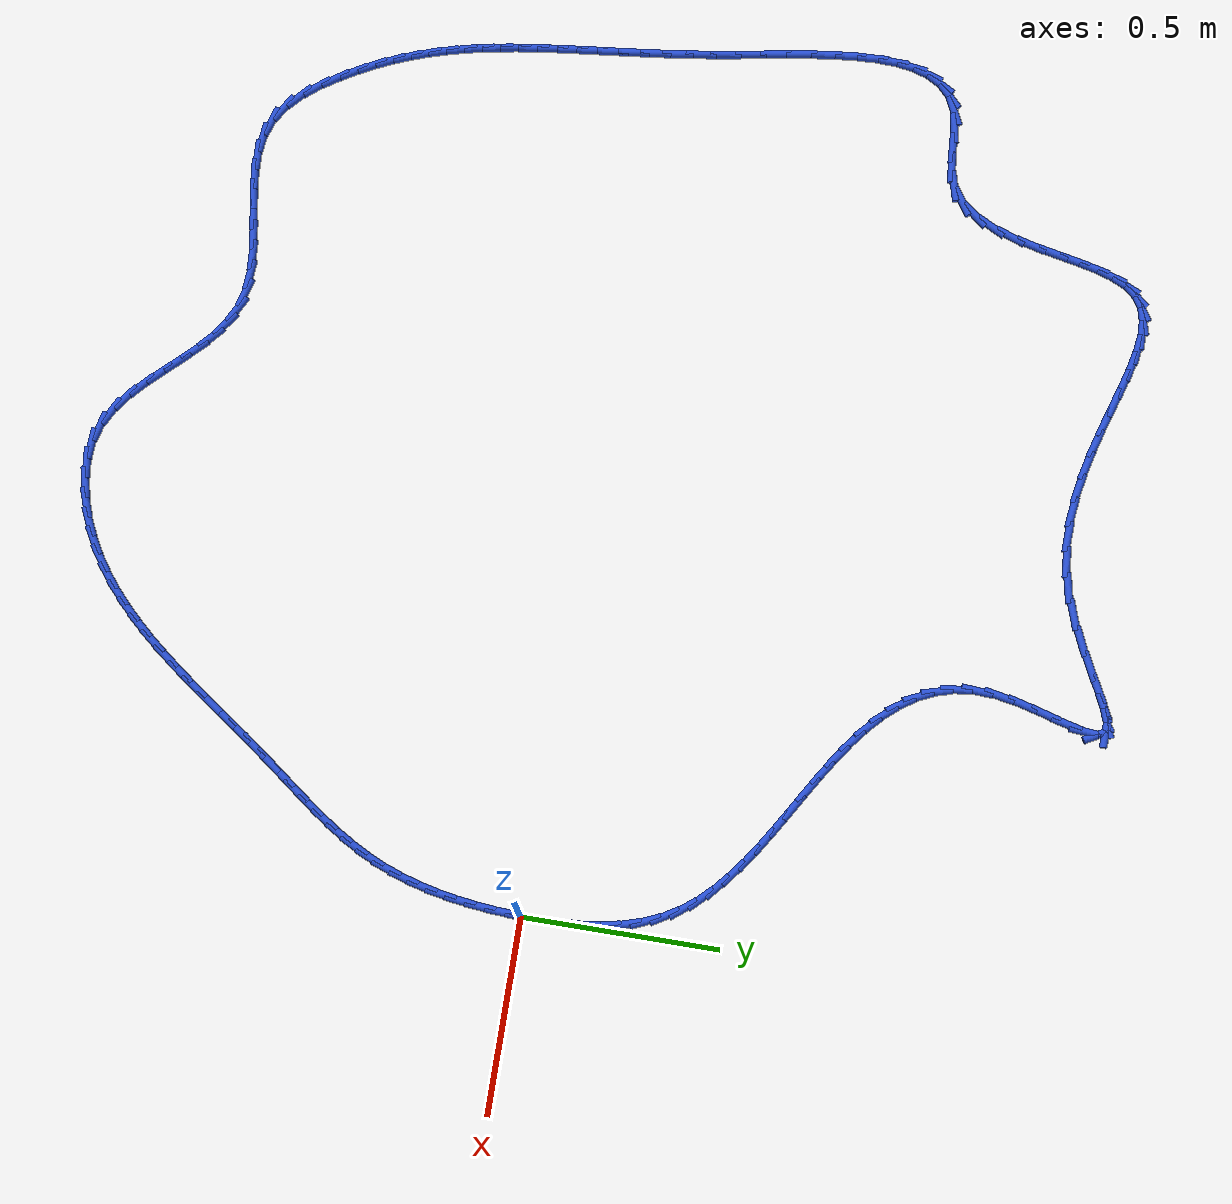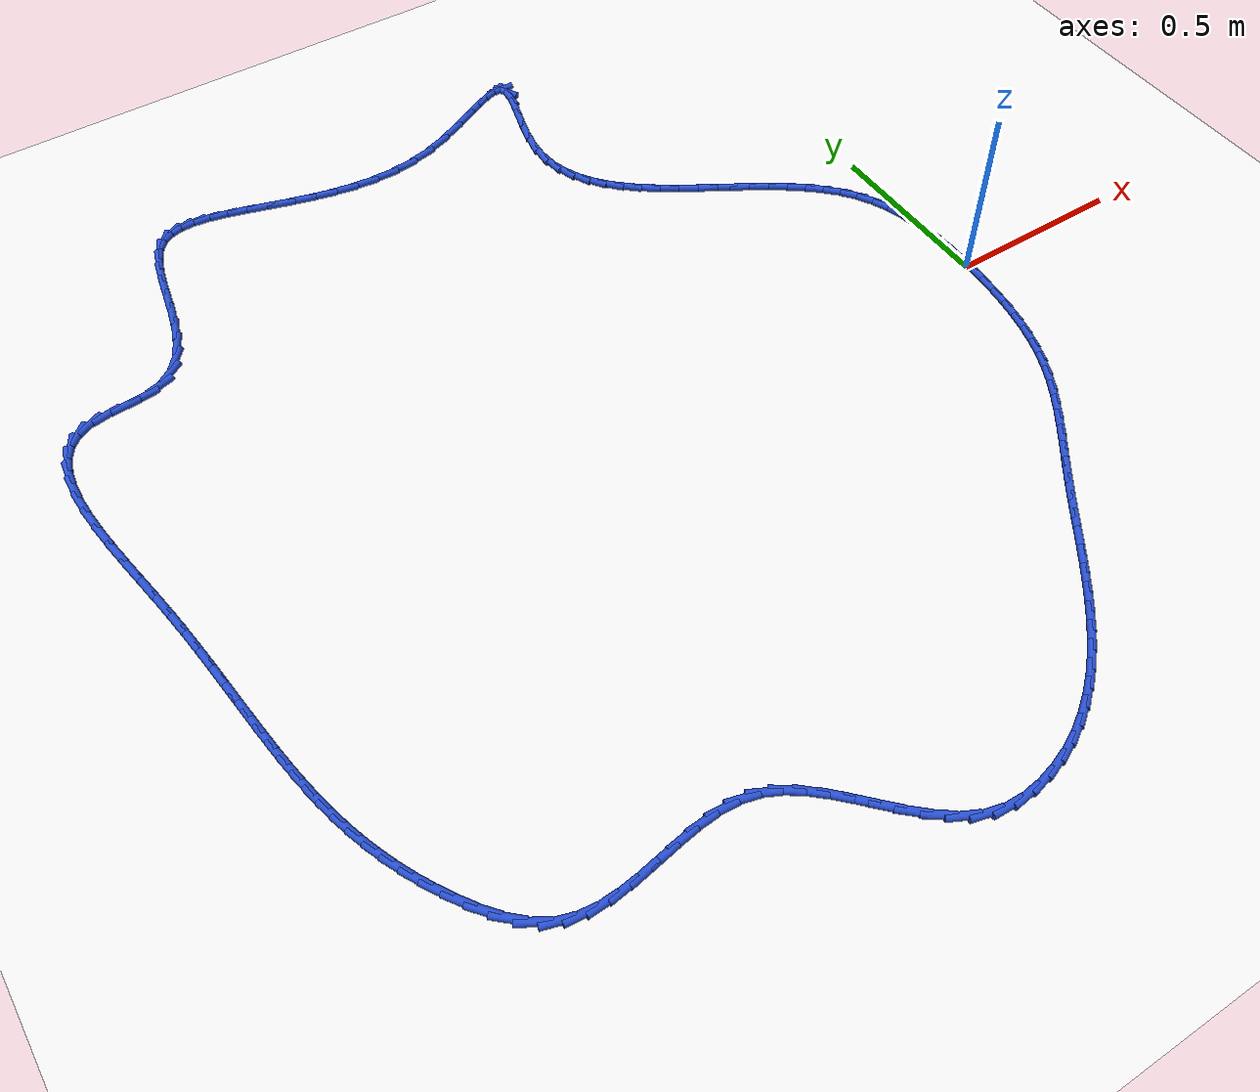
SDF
<sdf version="1.6">
 <world name="default">
  <light name="sun" type="directional">
   <pose>0 0 10 0 -0 0</pose>
   <diffuse>0.8 0.8 0.8 1</diffuse>
   <specular>0.2 0.2 0.2 1</specular>
   <attenuation>
    <range>1000</range>
    <constant>0.9</constant>
    <linear>0.01</linear>
    <quadratic>0.001</quadratic>
   </attenuation>
   <direction>-0.5 0.1 -0.9</direction>
  </light>
  <model name="ground_plane">
   <static>1</static>
   <link name="link">
    <collision name="collision">
     <geometry><plane><normal>0 0 1</normal><size>100 100</size></plane></geometry>
     <surface><friction><ode><mu>100</mu><mu2>50</mu2></ode></friction></surface>
    </collision>
    <visual name="visual">
     <cast_shadows>0</cast_shadows>
     <geometry><plane><normal>0 0 1</normal><size>100 100</size></plane></geometry>
     <material>
      <script><uri>file://media/materials/scripts/gazebo.material</uri><name>Gazebo/WhiteGlow</name></script>
     </material>
    </visual>
   </link>
  </model>
  <gravity>0 0 -9.8</gravity>
  <magnetic_field>6e-06 2.3e-05 -4.2e-05</magnetic_field>
  <atmosphere type="adiabatic"/>
  <physics name="default_physics" default="0" type="ode">
   <max_step_size>0.001</max_step_size>
   <real_time_factor>1</real_time_factor>
   <real_time_update_rate>1000</real_time_update_rate>
  </physics>
  <scene><ambient>0.4 0.4 0.4 1</ambient><background>0.7 0.7 0.7 1</background><shadows>1</shadows></scene>
  <spherical_coordinates>
   <surface_model>EARTH_WGS84</surface_model>
   <latitude_deg>0</latitude_deg>
   <longitude_deg>0</longitude_deg>
   <elevation>0</elevation>
   <heading_deg>0</heading_deg>
  </spherical_coordinates>
  <model name="line">
   <link name="link_0">
    <pose>4.5102810375396984e-17 0.0 0.01 0 1.57 1.5543094078143833</pose>
    <collision name="collision">
     <geometry><cylinder><radius>0.01</radius><length>0.08</length></cylinder></geometry>
    </collision>
    <visual name="visual">
     <material>
      <script><name>Gazebo/Blue</name><uri>file://media/materials/scripts/gazebo.material</uri></script>
     </material>
     <geometry><cylinder><radius>0.01</radius><length>0.08</length></cylinder></geometry>
    </visual>
   </link>
   <link name="link_1">
    <pose>0.0008690291871561428 0.05270544771607257 0.01 0 1.57 -1.5477289042147233</pose>
    <collision name="collision">
     <geometry><cylinder><radius>0.01</radius><length>0.08</length></cylinder></geometry>
    </collision>
    <visual name="visual">
     <material>
      <script><name>Gazebo/Blue</name><uri>file://media/materials/scripts/gazebo.material</uri></script>
     </material>
     <geometry><cylinder><radius>0.01</radius><length>0.08</length></cylinder></geometry>
    </visual>
   </link>
   <link name="link_2">
    <pose>-0.0003457334321145674 0.10535750047948886 0.01 0 1.57 -1.4967418213716803</pose>
    <collision name="collision">
     <geometry><cylinder><radius>0.01</radius><length>0.08</length></cylinder></geometry>
    </collision>
    <visual name="visual">
     <material>
      <script><name>Gazebo/Blue</name><uri>file://media/materials/scripts/gazebo.material</uri></script>
     </material>
     <geometry><cylinder><radius>0.01</radius><length>0.08</length></cylinder></geometry>
    </visual>
   </link>
   <link name="link_3">
    <pose>-0.00421222070409771 0.15747339316978526 0.01 0 1.57 -1.4329949120833474</pose>
    <collision name="collision">
     <geometry><cylinder><radius>0.01</radius><length>0.08</length></cylinder></geometry>
    </collision>
    <visual name="visual">
     <material>
      <script><name>Gazebo/Blue</name><uri>file://media/materials/scripts/gazebo.material</uri></script>
     </material>
     <geometry><cylinder><radius>0.01</radius><length>0.08</length></cylinder></geometry>
    </visual>
   </link>
   <link name="link_4">
    <pose>-0.011298365475078918 0.208570360666498 0.01 0 1.57 -1.35496207583835</pose>
    <collision name="collision">
     <geometry><cylinder><radius>0.01</radius><length>0.08</length></cylinder></geometry>
    </collision>
    <visual name="visual">
     <material>
      <script><name>Gazebo/Blue</name><uri>file://media/materials/scripts/gazebo.material</uri></script>
     </material>
     <geometry><cylinder><radius>0.01</radius><length>0.08</length></cylinder></geometry>
    </visual>
   </link>
   <link name="link_5">
    <pose>-0.02217210059134382 0.25816563784916363 0.01 0 1.57 -1.261211601704958</pose>
    <collision name="collision">
     <geometry><cylinder><radius>0.01</radius><length>0.08</length></cylinder></geometry>
    </collision>
    <visual name="visual">
     <material>
      <script><name>Gazebo/Blue</name><uri>file://media/materials/scripts/gazebo.material</uri></script>
     </material>
     <geometry><cylinder><radius>0.01</radius><length>0.08</length></cylinder></geometry>
    </visual>
   </link>
   <link name="link_6">
    <pose>-0.03740135889917806 0.3057764595973184 0.01 0 1.57 -1.1509289118824793</pose>
    <collision name="collision">
     <geometry><cylinder><radius>0.01</radius><length>0.08</length></cylinder></geometry>
    </collision>
    <visual name="visual">
     <material>
      <script><name>Gazebo/Blue</name><uri>file://media/materials/scripts/gazebo.material</uri></script>
     </material>
     <geometry><cylinder><radius>0.01</radius><length>0.08</length></cylinder></geometry>
    </visual>
   </link>
   <link name="link_7">
    <pose>-0.05755407324486725 0.3509200607904987 0.01 0 1.57 -1.0247734232484178</pose>
    <collision name="collision">
     <geometry><cylinder><radius>0.01</radius><length>0.08</length></cylinder></geometry>
    </collision>
    <visual name="visual">
     <material>
      <script><name>Gazebo/Blue</name><uri>file://media/materials/scripts/gazebo.material</uri></script>
     </material>
     <geometry><cylinder><radius>0.01</radius><length>0.08</length></cylinder></geometry>
    </visual>
   </link>
   <link name="link_8">
    <pose>-0.08319441029813715 0.3931162070621145 0.01 0 1.57 -0.8959504965834816</pose>
    <collision name="collision">
     <geometry><cylinder><radius>0.01</radius><length>0.08</length></cylinder></geometry>
    </collision>
    <visual name="visual">
     <material>
      <script><name>Gazebo/Blue</name><uri>file://media/materials/scripts/gazebo.material</uri></script>
     </material>
     <geometry><cylinder><radius>0.01</radius><length>0.08</length></cylinder></geometry>
    </visual>
   </link>
   <link name="link_9">
    <pose>-0.11445036875524879 0.432177755399872 0.01 0 1.57 -0.7873207353098906</pose>
    <collision name="collision">
     <geometry><cylinder><radius>0.01</radius><length>0.08</length></cylinder></geometry>
    </collision>
    <visual name="visual">
     <material>
      <script><name>Gazebo/Blue</name><uri>file://media/materials/scripts/gazebo.material</uri></script>
     </material>
     <geometry><cylinder><radius>0.01</radius><length>0.08</length></cylinder></geometry>
    </visual>
   </link>
   <link name="link_10">
    <pose>-0.15061315529729935 0.46847986108000145 0.01 0 1.57 -0.7009551060248204</pose>
    <collision name="collision">
     <geometry><cylinder><radius>0.01</radius><length>0.08</length></cylinder></geometry>
    </collision>
    <visual name="visual">
     <material>
      <script><name>Gazebo/Blue</name><uri>file://media/materials/scripts/gazebo.material</uri></script>
     </material>
     <geometry><cylinder><radius>0.01</radius><length>0.08</length></cylinder></geometry>
    </visual>
   </link>
   <link name="link_11">
    <pose>-0.190879258121659 0.5024613272629463 0.01 0 1.57 -0.635003452888492</pose>
    <collision name="collision">
     <geometry><cylinder><radius>0.01</radius><length>0.08</length></cylinder></geometry>
    </collision>
    <visual name="visual">
     <material>
      <script><name>Gazebo/Blue</name><uri>file://media/materials/scripts/gazebo.material</uri></script>
     </material>
     <geometry><cylinder><radius>0.01</radius><length>0.08</length></cylinder></geometry>
    </visual>
   </link>
   <link name="link_12">
    <pose>-0.23444516542569777 0.5345609571091497 0.01 0 1.57 -0.5872276156693199</pose>
    <collision name="collision">
     <geometry><cylinder><radius>0.01</radius><length>0.08</length></cylinder></geometry>
    </collision>
    <visual name="visual">
     <material>
      <script><name>Gazebo/Blue</name><uri>file://media/materials/scripts/gazebo.material</uri></script>
     </material>
     <geometry><cylinder><radius>0.01</radius><length>0.08</length></cylinder></geometry>
    </visual>
   </link>
   <link name="link_13">
    <pose>-0.2805073654067858 0.5652175537790549 0.01 0 1.57 -0.5556651994651087</pose>
    <collision name="collision">
     <geometry><cylinder><radius>0.01</radius><length>0.08</length></cylinder></geometry>
    </collision>
    <visual name="visual">
     <material>
      <script><name>Gazebo/Blue</name><uri>file://media/materials/scripts/gazebo.material</uri></script>
     </material>
     <geometry><cylinder><radius>0.01</radius><length>0.08</length></cylinder></geometry>
    </visual>
   </link>
   <link name="link_14">
    <pose>-0.32826234626229306 0.5948699204331053 0.01 0 1.57 -0.5389124581091073</pose>
    <collision name="collision">
     <geometry><cylinder><radius>0.01</radius><length>0.08</length></cylinder></geometry>
    </collision>
    <visual name="visual">
     <material>
      <script><name>Gazebo/Blue</name><uri>file://media/materials/scripts/gazebo.material</uri></script>
     </material>
     <geometry><cylinder><radius>0.01</radius><length>0.08</length></cylinder></geometry>
    </visual>
   </link>
   <link name="link_15">
    <pose>-0.3769065961895898 0.6239568602317438 0.01 0 1.57 -0.5362188868014457</pose>
    <collision name="collision">
     <geometry><cylinder><radius>0.01</radius><length>0.08</length></cylinder></geometry>
    </collision>
    <visual name="visual">
     <material>
      <script><name>Gazebo/Blue</name><uri>file://media/materials/scripts/gazebo.material</uri></script>
     </material>
     <geometry><cylinder><radius>0.01</radius><length>0.08</length></cylinder></geometry>
    </visual>
   </link>
   <link name="link_16">
    <pose>-0.4256366033860461 0.6529171763354139 0.01 0 1.57 -0.5475126127471217</pose>
    <collision name="collision">
     <geometry><cylinder><radius>0.01</radius><length>0.08</length></cylinder></geometry>
    </collision>
    <visual name="visual">
     <material>
      <script><name>Gazebo/Blue</name><uri>file://media/materials/scripts/gazebo.material</uri></script>
     </material>
     <geometry><cylinder><radius>0.01</radius><length>0.08</length></cylinder></geometry>
    </visual>
   </link>
   <link name="link_17">
    <pose>-0.4736488560490321 0.6821896719045591 0.01 0 1.57 -0.5734109201992059</pose>
    <collision name="collision">
     <geometry><cylinder><radius>0.01</radius><length>0.08</length></cylinder></geometry>
    </collision>
    <visual name="visual">
     <material>
      <script><name>Gazebo/Blue</name><uri>file://media/materials/scripts/gazebo.material</uri></script>
     </material>
     <geometry><cylinder><radius>0.01</radius><length>0.08</length></cylinder></geometry>
    </visual>
   </link>
   <link name="link_18">
    <pose>-0.5201398423759176 0.712213150099622 0.01 0 1.57 -0.6152236396197325</pose>
    <collision name="collision">
     <geometry><cylinder><radius>0.01</radius><length>0.08</length></cylinder></geometry>
    </collision>
    <visual name="visual">
     <material>
      <script><name>Gazebo/Blue</name><uri>file://media/materials/scripts/gazebo.material</uri></script>
     </material>
     <geometry><cylinder><radius>0.01</radius><length>0.08</length></cylinder></geometry>
    </visual>
   </link>
   <link name="link_19">
    <pose>-0.5643060505640731 0.7434264140810467 0.01 0 1.57 -0.6749120622801789</pose>
    <collision name="collision">
     <geometry><cylinder><radius>0.01</radius><length>0.08</length></cylinder></geometry>
    </collision>
    <visual name="visual">
     <material>
      <script><name>Gazebo/Blue</name><uri>file://media/materials/scripts/gazebo.material</uri></script>
     </material>
     <geometry><cylinder><radius>0.01</radius><length>0.08</length></cylinder></geometry>
    </visual>
   </link>
   <link name="link_20">
    <pose>-0.6053439688108685 0.7762682670092759 0.01 0 1.57 -0.7549020256641142</pose>
    <collision name="collision">
     <geometry><cylinder><radius>0.01</radius><length>0.08</length></cylinder></geometry>
    </collision>
    <visual name="visual">
     <material>
      <script><name>Gazebo/Blue</name><uri>file://media/materials/scripts/gazebo.material</uri></script>
     </material>
     <geometry><cylinder><radius>0.01</radius><length>0.08</length></cylinder></geometry>
    </visual>
   </link>
   <link name="link_21">
    <pose>-0.6424500853136739 0.811177512044753 0.01 0 1.57 -0.8575596352595629</pose>
    <collision name="collision">
     <geometry><cylinder><radius>0.01</radius><length>0.08</length></cylinder></geometry>
    </collision>
    <visual name="visual">
     <material>
      <script><name>Gazebo/Blue</name><uri>file://media/materials/scripts/gazebo.material</uri></script>
     </material>
     <geometry><cylinder><radius>0.01</radius><length>0.08</length></cylinder></geometry>
    </visual>
   </link>
   <link name="link_22">
    <pose>-0.6748208882698594 0.8485929523479212 0.01 0 1.57 -0.9840809942317578</pose>
    <collision name="collision">
     <geometry><cylinder><radius>0.01</radius><length>0.08</length></cylinder></geometry>
    </collision>
    <visual name="visual">
     <material>
      <script><name>Gazebo/Blue</name><uri>file://media/materials/scripts/gazebo.material</uri></script>
     </material>
     <geometry><cylinder><radius>0.01</radius><length>0.08</length></cylinder></geometry>
    </visual>
   </link>
   <link name="link_23">
    <pose>-0.7016528658767949 0.8889533910792238 0.01 0 1.57 -1.1327497866986338</pose>
    <collision name="collision">
     <geometry><cylinder><radius>0.01</radius><length>0.08</length></cylinder></geometry>
    </collision>
    <visual name="visual">
     <material>
      <script><name>Gazebo/Blue</name><uri>file://media/materials/scripts/gazebo.material</uri></script>
     </material>
     <geometry><cylinder><radius>0.01</radius><length>0.08</length></cylinder></geometry>
    </visual>
   </link>
   <link name="link_24">
    <pose>-0.722142506331851 0.9326976313991041 0.01 0 1.57 -1.2972988642377445</pose>
    <collision name="collision">
     <geometry><cylinder><radius>0.01</radius><length>0.08</length></cylinder></geometry>
    </collision>
    <visual name="visual">
     <material>
      <script><name>Gazebo/Blue</name><uri>file://media/materials/scripts/gazebo.material</uri></script>
     </material>
     <geometry><cylinder><radius>0.01</radius><length>0.08</length></cylinder></geometry>
    </visual>
   </link>
   <link name="link_25">
    <pose>-0.7354862978323973 0.9802644764680052 0.01 0 1.57 -1.4670869333536785</pose>
    <collision name="collision">
     <geometry><cylinder><radius>0.01</radius><length>0.08</length></cylinder></geometry>
    </collision>
    <visual name="visual">
     <material>
      <script><name>Gazebo/Blue</name><uri>file://media/materials/scripts/gazebo.material</uri></script>
     </material>
     <geometry><cylinder><radius>0.01</radius><length>0.08</length></cylinder></geometry>
    </visual>
   </link>
   <link name="link_26">
    <pose>-0.7408807285758041 1.0320927294463704 0.01 0 1.57 1.5115718175551986</pose>
    <collision name="collision">
     <geometry><cylinder><radius>0.01</radius><length>0.08</length></cylinder></geometry>
    </collision>
    <visual name="visual">
     <material>
      <script><name>Gazebo/Blue</name><uri>file://media/materials/scripts/gazebo.material</uri></script>
     </material>
     <geometry><cylinder><radius>0.01</radius><length>0.08</length></cylinder></geometry>
    </visual>
   </link>
   <link name="link_27">
    <pose>-0.7375293241366412 1.0886146857738823 0.01 0 1.57 1.3831997076289502</pose>
    <collision name="collision">
     <geometry><cylinder><radius>0.01</radius><length>0.08</length></cylinder></geometry>
    </collision>
    <visual name="visual">
     <material>
      <script><name>Gazebo/Blue</name><uri>file://media/materials/scripts/gazebo.material</uri></script>
     </material>
     <geometry><cylinder><radius>0.01</radius><length>0.08</length></cylinder></geometry>
    </visual>
   </link>
   <link name="link_28">
    <pose>-0.7260803915679791 1.1489265984761414 0.01 0 1.57 1.3158758738875893</pose>
    <collision name="collision">
     <geometry><cylinder><radius>0.01</radius><length>0.08</length></cylinder></geometry>
    </collision>
    <visual name="visual">
     <material>
      <script><name>Gazebo/Blue</name><uri>file://media/materials/scripts/gazebo.material</uri></script>
     </material>
     <geometry><cylinder><radius>0.01</radius><length>0.08</length></cylinder></geometry>
    </visual>
   </link>
   <link name="link_29">
    <pose>-0.7103828869187819 1.2091649630827312 0.01 0 1.57 1.2975483605151854</pose>
    <collision name="collision">
     <geometry><cylinder><radius>0.01</radius><length>0.08</length></cylinder></geometry>
    </collision>
    <visual name="visual">
     <material>
      <script><name>Gazebo/Blue</name><uri>file://media/materials/scripts/gazebo.material</uri></script>
     </material>
     <geometry><cylinder><radius>0.01</radius><length>0.08</length></cylinder></geometry>
    </visual>
   </link>
   <link name="link_30">
    <pose>-0.6947153157893236 1.2650690549013248 0.01 0 1.57 1.3351524285173113</pose>
    <collision name="collision">
     <geometry><cylinder><radius>0.01</radius><length>0.08</length></cylinder></geometry>
    </collision>
    <visual name="visual">
     <material>
      <script><name>Gazebo/Blue</name><uri>file://media/materials/scripts/gazebo.material</uri></script>
     </material>
     <geometry><cylinder><radius>0.01</radius><length>0.08</length></cylinder></geometry>
    </visual>
   </link>
   <link name="link_31">
    <pose>-0.6833561837798791 1.312378149239597 0.01 0 1.57 1.4905072942985023</pose>
    <collision name="collision">
     <geometry><cylinder><radius>0.01</radius><length>0.08</length></cylinder></geometry>
    </collision>
    <visual name="visual">
     <material>
      <script><name>Gazebo/Blue</name><uri>file://media/materials/scripts/gazebo.material</uri></script>
     </material>
     <geometry><cylinder><radius>0.01</radius><length>0.08</length></cylinder></geometry>
    </visual>
   </link>
   <link name="link_32">
    <pose>-0.6805839964907223 1.3468315214052202 0.01 0 1.57 -1.054722958687675</pose>
    <collision name="collision">
     <geometry><cylinder><radius>0.01</radius><length>0.08</length></cylinder></geometry>
    </collision>
    <visual name="visual">
     <material>
      <script><name>Gazebo/Blue</name><uri>file://media/materials/scripts/gazebo.material</uri></script>
     </material>
     <geometry><cylinder><radius>0.01</radius><length>0.08</length></cylinder></geometry>
    </visual>
   </link>
   <link name="link_33">
    <pose>-0.6905287214718429 1.3643596019786333 0.01 0 1.57 -0.021457759578437773</pose>
    <collision name="collision">
     <geometry><cylinder><radius>0.01</radius><length>0.08</length></cylinder></geometry>
    </collision>
    <visual name="visual">
     <material>
      <script><name>Gazebo/Blue</name><uri>file://media/materials/scripts/gazebo.material</uri></script>
     </material>
     <geometry><cylinder><radius>0.01</radius><length>0.08</length></cylinder></geometry>
    </visual>
   </link>
   <link name="link_34">
    <pose>-0.7142311774067759 1.3648682816532844 0.01 0 1.57 0.3465531213698885</pose>
    <collision name="collision">
     <geometry><cylinder><radius>0.01</radius><length>0.08</length></cylinder></geometry>
    </collision>
    <visual name="visual">
     <material>
      <script><name>Gazebo/Blue</name><uri>file://media/materials/scripts/gazebo.material</uri></script>
     </material>
     <geometry><cylinder><radius>0.01</radius><length>0.08</length></cylinder></geometry>
    </visual>
   </link>
   <link name="link_35">
    <pose>-0.7498145808449191 1.3520181458334757 0.01 0 1.57 0.4577317803803484</pose>
    <collision name="collision">
     <geometry><cylinder><radius>0.01</radius><length>0.08</length></cylinder></geometry>
    </collision>
    <visual name="visual">
     <material>
      <script><name>Gazebo/Blue</name><uri>file://media/materials/scripts/gazebo.material</uri></script>
     </material>
     <geometry><cylinder><radius>0.01</radius><length>0.08</length></cylinder></geometry>
    </visual>
   </link>
   <link name="link_36">
    <pose>-0.795287954743603 1.329616736930131 0.01 0 1.57 0.48527604367075133</pose>
    <collision name="collision">
     <geometry><cylinder><radius>0.01</radius><length>0.08</length></cylinder></geometry>
    </collision>
    <visual name="visual">
     <material>
      <script><name>Gazebo/Blue</name><uri>file://media/materials/scripts/gazebo.material</uri></script>
     </material>
     <geometry><cylinder><radius>0.01</radius><length>0.08</length></cylinder></geometry>
    </visual>
   </link>
   <link name="link_37">
    <pose>-0.8486603220601575 1.3014715973541744 0.01 0 1.57 0.4695830852292554</pose>
    <collision name="collision">
     <geometry><cylinder><radius>0.01</radius><length>0.08</length></cylinder></geometry>
    </collision>
    <visual name="visual">
     <material>
      <script><name>Gazebo/Blue</name><uri>file://media/materials/scripts/gazebo.material</uri></script>
     </material>
     <geometry><cylinder><radius>0.01</radius><length>0.08</length></cylinder></geometry>
    </visual>
   </link>
   <link name="link_38">
    <pose>-0.9079407057519127 1.2713902695165296 0.01 0 1.57 0.4198382427069961</pose>
    <collision name="collision">
     <geometry><cylinder><radius>0.01</radius><length>0.08</length></cylinder></geometry>
    </collision>
    <visual name="visual">
     <material>
      <script><name>Gazebo/Blue</name><uri>file://media/materials/scripts/gazebo.material</uri></script>
     </material>
     <geometry><cylinder><radius>0.01</radius><length>0.08</length></cylinder></geometry>
    </visual>
   </link>
   <link name="link_39">
    <pose>-0.9711381287761987 1.24318029582812 0.01 0 1.57 0.33308429898072217</pose>
    <collision name="collision">
     <geometry><cylinder><radius>0.01</radius><length>0.08</length></cylinder></geometry>
    </collision>
    <visual name="visual">
     <material>
      <script><name>Gazebo/Blue</name><uri>file://media/materials/scripts/gazebo.material</uri></script>
     </material>
     <geometry><cylinder><radius>0.01</radius><length>0.08</length></cylinder></geometry>
    </visual>
   </link>
   <link name="link_40">
    <pose>-1.0362616140903458 1.2206492186998699 0.01 0 1.57 0.20851420240404975</pose>
    <collision name="collision">
     <geometry><cylinder><radius>0.01</radius><length>0.08</length></cylinder></geometry>
    </collision>
    <visual name="visual">
     <material>
      <script><name>Gazebo/Blue</name><uri>file://media/materials/scripts/gazebo.material</uri></script>
     </material>
     <geometry><cylinder><radius>0.01</radius><length>0.08</length></cylinder></geometry>
    </visual>
   </link>
   <link name="link_41">
    <pose>-1.1015689173653462 1.2068308700375336 0.01 0 1.57 0.08446068056832406</pose>
    <collision name="collision">
     <geometry><cylinder><radius>0.01</radius><length>0.08</length></cylinder></geometry>
    </collision>
    <visual name="visual">
     <material>
      <script><name>Gazebo/Blue</name><uri>file://media/materials/scripts/gazebo.material</uri></script>
     </material>
     <geometry><cylinder><radius>0.01</radius><length>0.08</length></cylinder></geometry>
    </visual>
   </link>
   <link name="link_42">
    <pose>-1.1664167308378783 1.201340718505173 0.01 0 1.57 -0.023567856361768745</pose>
    <collision name="collision">
     <geometry><cylinder><radius>0.01</radius><length>0.08</length></cylinder></geometry>
    </collision>
    <visual name="visual">
     <material>
      <script><name>Gazebo/Blue</name><uri>file://media/materials/scripts/gazebo.material</uri></script>
     </material>
     <geometry><cylinder><radius>0.01</radius><length>0.08</length></cylinder></geometry>
    </visual>
   </link>
   <link name="link_43">
    <pose>-1.2304651441073151 1.2028504818492476 0.01 0 1.57 -0.1136625856904056</pose>
    <collision name="collision">
     <geometry><cylinder><radius>0.01</radius><length>0.08</length></cylinder></geometry>
    </collision>
    <visual name="visual">
     <material>
      <script><name>Gazebo/Blue</name><uri>file://media/materials/scripts/gazebo.material</uri></script>
     </material>
     <geometry><cylinder><radius>0.01</radius><length>0.08</length></cylinder></geometry>
    </visual>
   </link>
   <link name="link_44">
    <pose>-1.293374256770968 1.210031846716526 0.01 0 1.57 -0.18545086745416847</pose>
    <collision name="collision">
     <geometry><cylinder><radius>0.01</radius><length>0.08</length></cylinder></geometry>
    </collision>
    <visual name="visual">
     <material>
      <script><name>Gazebo/Blue</name><uri>file://media/materials/scripts/gazebo.material</uri></script>
     </material>
     <geometry><cylinder><radius>0.01</radius><length>0.08</length></cylinder></geometry>
    </visual>
   </link>
   <link name="link_45">
    <pose>-1.354804168426147 1.2215564997537771 0.01 0 1.57 -0.2392380259000711</pose>
    <collision name="collision">
     <geometry><cylinder><radius>0.01</radius><length>0.08</length></cylinder></geometry>
    </collision>
    <visual name="visual">
     <material>
      <script><name>Gazebo/Blue</name><uri>file://media/materials/scripts/gazebo.material</uri></script>
     </material>
     <geometry><cylinder><radius>0.01</radius><length>0.08</length></cylinder></geometry>
    </visual>
   </link>
   <link name="link_46">
    <pose>-1.4144149786701639 1.2360961276077704 0.01 0 1.57 -0.2752634387611954</pose>
    <collision name="collision">
     <geometry><cylinder><radius>0.01</radius><length>0.08</length></cylinder></geometry>
    </collision>
    <visual name="visual">
     <material>
      <script><name>Gazebo/Blue</name><uri>file://media/materials/scripts/gazebo.material</uri></script>
     </material>
     <geometry><cylinder><radius>0.01</radius><length>0.08</length></cylinder></geometry>
    </visual>
   </link>
   <link name="link_47">
    <pose>-1.4718667871003281 1.2523224169252742 0.01 0 1.57 -0.29310485521868407</pose>
    <collision name="collision">
     <geometry><cylinder><radius>0.01</radius><length>0.08</length></cylinder></geometry>
    </collision>
    <visual name="visual">
     <material>
      <script><name>Gazebo/Blue</name><uri>file://media/materials/scripts/gazebo.material</uri></script>
     </material>
     <geometry><cylinder><radius>0.01</radius><length>0.08</length></cylinder></geometry>
    </visual>
   </link>
   <link name="link_48">
    <pose>-1.5268196933139528 1.268907054353059 0.01 0 1.57 -0.29111243871311804</pose>
    <collision name="collision">
     <geometry><cylinder><radius>0.01</radius><length>0.08</length></cylinder></geometry>
    </collision>
    <visual name="visual">
     <material>
      <script><name>Gazebo/Blue</name><uri>file://media/materials/scripts/gazebo.material</uri></script>
     </material>
     <geometry><cylinder><radius>0.01</radius><length>0.08</length></cylinder></geometry>
    </visual>
   </link>
   <link name="link_49">
    <pose>-1.5789337969083475 1.2845217265378923 0.01 0 1.57 -0.265688489030506</pose>
    <collision name="collision">
     <geometry><cylinder><radius>0.01</radius><length>0.08</length></cylinder></geometry>
    </collision>
    <visual name="visual">
     <material>
      <script><name>Gazebo/Blue</name><uri>file://media/materials/scripts/gazebo.material</uri></script>
     </material>
     <geometry><cylinder><radius>0.01</radius><length>0.08</length></cylinder></geometry>
    </visual>
   </link>
   <link name="link_50">
    <pose>-1.6278691974808233 1.2978381201265443 0.01 0 1.57 -0.21020122273331251</pose>
    <collision name="collision">
     <geometry><cylinder><radius>0.01</radius><length>0.08</length></cylinder></geometry>
    </collision>
    <visual name="visual">
     <material>
      <script><name>Gazebo/Blue</name><uri>file://media/materials/scripts/gazebo.material</uri></script>
     </material>
     <geometry><cylinder><radius>0.01</radius><length>0.08</length></cylinder></geometry>
    </visual>
   </link>
   <link name="link_51">
    <pose>-1.6732859946286915 1.3075279217657834 0.01 0 1.57 -0.11344466511503097</pose>
    <collision name="collision">
     <geometry><cylinder><radius>0.01</radius><length>0.08</length></cylinder></geometry>
    </collision>
    <visual name="visual">
     <material>
      <script><name>Gazebo/Blue</name><uri>file://media/materials/scripts/gazebo.material</uri></script>
     </material>
     <geometry><cylinder><radius>0.01</radius><length>0.08</length></cylinder></geometry>
    </visual>
   </link>
   <link name="link_52">
    <pose>-1.7148442879492634 1.312262818102379 0.01 0 1.57 0.04141973717026323</pose>
    <collision name="collision">
     <geometry><cylinder><radius>0.01</radius><length>0.08</length></cylinder></geometry>
    </collision>
    <visual name="visual">
     <material>
      <script><name>Gazebo/Blue</name><uri>file://media/materials/scripts/gazebo.material</uri></script>
     </material>
     <geometry><cylinder><radius>0.01</radius><length>0.08</length></cylinder></geometry>
    </visual>
   </link>
   <link name="link_53">
    <pose>-1.752204177039849 1.3107144957831 0.01 0 1.57 0.2721555685332228</pose>
    <collision name="collision">
     <geometry><cylinder><radius>0.01</radius><length>0.08</length></cylinder></geometry>
    </collision>
    <visual name="visual">
     <material>
      <script><name>Gazebo/Blue</name><uri>file://media/materials/scripts/gazebo.material</uri></script>
     </material>
     <geometry><cylinder><radius>0.01</radius><length>0.08</length></cylinder></geometry>
    </visual>
   </link>
   <link name="link_54">
    <pose>-1.78502576149776 1.3015546414547157 0.01 0 1.57 0.5747761326183344</pose>
    <collision name="collision">
     <geometry><cylinder><radius>0.01</radius><length>0.08</length></cylinder></geometry>
    </collision>
    <visual name="visual">
     <material>
      <script><name>Gazebo/Blue</name><uri>file://media/materials/scripts/gazebo.material</uri></script>
     </material>
     <geometry><cylinder><radius>0.01</radius><length>0.08</length></cylinder></geometry>
    </visual>
   </link>
   <link name="link_55">
    <pose>-1.8129691409203068 1.2834549417639949 0.01 0 1.57 0.8952498651201162</pose>
    <collision name="collision">
     <geometry><cylinder><radius>0.01</radius><length>0.08</length></cylinder></geometry>
    </collision>
    <visual name="visual">
     <material>
      <script><name>Gazebo/Blue</name><uri>file://media/materials/scripts/gazebo.material</uri></script>
     </material>
     <geometry><cylinder><radius>0.01</radius><length>0.08</length></cylinder></geometry>
    </visual>
   </link>
   <link name="link_56">
    <pose>-1.8356968674038447 1.2550921497712753 0.01 0 1.57 1.1437435690401714</pose>
    <collision name="collision">
     <geometry><cylinder><radius>0.01</radius><length>0.08</length></cylinder></geometry>
    </collision>
    <visual name="visual">
     <material>
      <script><name>Gazebo/Blue</name><uri>file://media/materials/scripts/gazebo.material</uri></script>
     </material>
     <geometry><cylinder><radius>0.01</radius><length>0.08</length></cylinder></geometry>
    </visual>
   </link>
   <link name="link_57">
    <pose>-1.8533892962799696 1.2162127051262561 0.01 0 1.57 1.2829893116486195</pose>
    <collision name="collision">
     <geometry><cylinder><radius>0.01</radius><length>0.08</length></cylinder></geometry>
    </collision>
    <visual name="visual">
     <material>
      <script><name>Gazebo/Blue</name><uri>file://media/materials/scripts/gazebo.material</uri></script>
     </material>
     <geometry><cylinder><radius>0.01</radius><length>0.08</length></cylinder></geometry>
    </visual>
   </link>
   <link name="link_58">
    <pose>-1.8673810276956342 1.1689475057357284 0.01 0 1.57 1.3528453523240942</pose>
    <collision name="collision">
     <geometry><cylinder><radius>0.01</radius><length>0.08</length></cylinder></geometry>
    </collision>
    <visual name="visual">
     <material>
      <script><name>Gazebo/Blue</name><uri>file://media/materials/scripts/gazebo.material</uri></script>
     </material>
     <geometry><cylinder><radius>0.01</radius><length>0.08</length></cylinder></geometry>
    </visual>
   </link>
   <link name="link_59">
    <pose>-1.8791626772312728 1.1157497488000603 0.01 0 1.57 1.3780406095152178</pose>
    <collision name="collision">
     <geometry><cylinder><radius>0.01</radius><length>0.08</length></cylinder></geometry>
    </collision>
    <visual name="visual">
     <material>
      <script><name>Gazebo/Blue</name><uri>file://media/materials/scripts/gazebo.material</uri></script>
     </material>
     <geometry><cylinder><radius>0.01</radius><length>0.08</length></cylinder></geometry>
    </visual>
   </link>
   <link name="link_60">
    <pose>-1.8902248604673204 1.0590726315196173 0.01 0 1.57 1.368528544960826</pose>
    <collision name="collision">
     <geometry><cylinder><radius>0.01</radius><length>0.08</length></cylinder></geometry>
    </collision>
    <visual name="visual">
     <material>
      <script><name>Gazebo/Blue</name><uri>file://media/materials/scripts/gazebo.material</uri></script>
     </material>
     <geometry><cylinder><radius>0.01</radius><length>0.08</length></cylinder></geometry>
    </visual>
   </link>
   <link name="link_61">
    <pose>-1.9020581929842115 1.0013693510947663 0.01 0 1.57 1.3253822828104822</pose>
    <collision name="collision">
     <geometry><cylinder><radius>0.01</radius><length>0.08</length></cylinder></geometry>
    </collision>
    <visual name="visual">
     <material>
      <script><name>Gazebo/Blue</name><uri>file://media/materials/scripts/gazebo.material</uri></script>
     </material>
     <geometry><cylinder><radius>0.01</radius><length>0.08</length></cylinder></geometry>
    </visual>
   </link>
   <link name="link_62">
    <pose>-1.9161532903623795 0.9450931047258738 0.01 0 1.57 1.2424962335736878</pose>
    <collision name="collision">
     <geometry><cylinder><radius>0.01</radius><length>0.08</length></cylinder></geometry>
    </collision>
    <visual name="visual">
     <material>
      <script><name>Gazebo/Blue</name><uri>file://media/materials/scripts/gazebo.material</uri></script>
     </material>
     <geometry><cylinder><radius>0.01</radius><length>0.08</length></cylinder></geometry>
    </visual>
   </link>
   <link name="link_63">
    <pose>-1.9340007681822604 0.892697089613306 0.01 0 1.57 1.1061214182087873</pose>
    <collision name="collision">
     <geometry><cylinder><radius>0.01</radius><length>0.08</length></cylinder></geometry>
    </collision>
    <visual name="visual">
     <material>
      <script><name>Gazebo/Blue</name><uri>file://media/materials/scripts/gazebo.material</uri></script>
     </material>
     <geometry><cylinder><radius>0.01</radius><length>0.08</length></cylinder></geometry>
    </visual>
   </link>
   <link name="link_64">
    <pose>-1.9570912420242876 0.8466345029574303 0.01 0 1.57 0.8960011336004077</pose>
    <collision name="collision">
     <geometry><cylinder><radius>0.01</radius><length>0.08</length></cylinder></geometry>
    </collision>
    <visual name="visual">
     <material>
      <script><name>Gazebo/Blue</name><uri>file://media/materials/scripts/gazebo.material</uri></script>
     </material>
     <geometry><cylinder><radius>0.01</radius><length>0.08</length></cylinder></geometry>
    </visual>
   </link>
   <link name="link_65">
    <pose>-1.9869153274688962 0.8093585419586122 0.01 0 1.57 0.6001053869498707</pose>
    <collision name="collision">
     <geometry><cylinder><radius>0.01</radius><length>0.08</length></cylinder></geometry>
    </collision>
    <visual name="visual">
     <material>
      <script><name>Gazebo/Blue</name><uri>file://media/materials/scripts/gazebo.material</uri></script>
     </material>
     <geometry><cylinder><radius>0.01</radius><length>0.08</length></cylinder></geometry>
    </visual>
   </link>
   <link name="link_66">
    <pose>-2.0249636400965203 0.7833224038172184 0.01 0 1.57 0.2766241663873046</pose>
    <collision name="collision">
     <geometry><cylinder><radius>0.01</radius><length>0.08</length></cylinder></geometry>
    </collision>
    <visual name="visual">
     <material>
      <script><name>Gazebo/Blue</name><uri>file://media/materials/scripts/gazebo.material</uri></script>
     </material>
     <geometry><cylinder><radius>0.01</radius><length>0.08</length></cylinder></geometry>
    </visual>
   </link>
   <link name="link_67">
    <pose>-2.0719656936237305 0.7699783852841191 0.01 0 1.57 0.09680928653053363</pose>
    <collision name="collision">
     <geometry><cylinder><radius>0.01</radius><length>0.08</length></cylinder></geometry>
    </collision>
    <visual name="visual">
     <material>
      <script><name>Gazebo/Blue</name><uri>file://media/materials/scripts/gazebo.material</uri></script>
     </material>
     <geometry><cylinder><radius>0.01</radius><length>0.08</length></cylinder></geometry>
    </visual>
   </link>
   <link name="link_68">
    <pose>-2.1241860838512183 0.7649071139405943 0.01 0 1.57 0.06427983328724608</pose>
    <collision name="collision">
     <geometry><cylinder><radius>0.01</radius><length>0.08</length></cylinder></geometry>
    </collision>
    <visual name="visual">
     <material>
      <script><name>Gazebo/Blue</name><uri>file://media/materials/scripts/gazebo.material</uri></script>
     </material>
     <geometry><cylinder><radius>0.01</radius><length>0.08</length></cylinder></geometry>
    </visual>
   </link>
   <link name="link_69">
    <pose>-2.1762663474905364 0.7615547848444852 0.01 0 1.57 0.17400628414478128</pose>
    <collision name="collision">
     <geometry><cylinder><radius>0.01</radius><length>0.08</length></cylinder></geometry>
    </collision>
    <visual name="visual">
     <material>
      <script><name>Gazebo/Blue</name><uri>file://media/materials/scripts/gazebo.material</uri></script>
     </material>
     <geometry><cylinder><radius>0.01</radius><length>0.08</length></cylinder></geometry>
    </visual>
   </link>
   <link name="link_70">
    <pose>-2.2228473934008677 0.7533665815193281 0.01 0 1.57 0.44689324955360427</pose>
    <collision name="collision">
     <geometry><cylinder><radius>0.01</radius><length>0.08</length></cylinder></geometry>
    </collision>
    <visual name="visual">
     <material>
      <script><name>Gazebo/Blue</name><uri>file://media/materials/scripts/gazebo.material</uri></script>
     </material>
     <geometry><cylinder><radius>0.01</radius><length>0.08</length></cylinder></geometry>
    </visual>
   </link>
   <link name="link_71">
    <pose>-2.26003079141365 0.7355472148341113 0.01 0 1.57 0.7718425095719428</pose>
    <collision name="collision">
     <geometry><cylinder><radius>0.01</radius><length>0.08</length></cylinder></geometry>
    </collision>
    <visual name="visual">
     <material>
      <script><name>Gazebo/Blue</name><uri>file://media/materials/scripts/gazebo.material</uri></script>
     </material>
     <geometry><cylinder><radius>0.01</radius><length>0.08</length></cylinder></geometry>
    </visual>
   </link>
   <link name="link_72">
    <pose>-2.2880494571421295 0.7082780576038216 0.01 0 1.57 1.063721684598557</pose>
    <collision name="collision">
     <geometry><cylinder><radius>0.01</radius><length>0.08</length></cylinder></geometry>
    </collision>
    <visual name="visual">
     <material>
      <script><name>Gazebo/Blue</name><uri>file://media/materials/scripts/gazebo.material</uri></script>
     </material>
     <geometry><cylinder><radius>0.01</radius><length>0.08</length></cylinder></geometry>
    </visual>
   </link>
   <link name="link_73">
    <pose>-2.3078616055890593 0.6726141858050402 0.01 0 1.57 1.2865488951452493</pose>
    <collision name="collision">
     <geometry><cylinder><radius>0.01</radius><length>0.08</length></cylinder></geometry>
    </collision>
    <visual name="visual">
     <material>
      <script><name>Gazebo/Blue</name><uri>file://media/materials/scripts/gazebo.material</uri></script>
     </material>
     <geometry><cylinder><radius>0.01</radius><length>0.08</length></cylinder></geometry>
    </visual>
   </link>
   <link name="link_74">
    <pose>-2.320425451757189 0.6296106754143486 0.01 0 1.57 1.444189596421528</pose>
    <collision name="collision">
     <geometry><cylinder><radius>0.01</radius><length>0.08</length></cylinder></geometry>
    </collision>
    <visual name="visual">
     <material>
      <script><name>Gazebo/Blue</name><uri>file://media/materials/scripts/gazebo.material</uri></script>
     </material>
     <geometry><cylinder><radius>0.01</radius><length>0.08</length></cylinder></geometry>
    </visual>
   </link>
   <link name="link_75">
    <pose>-2.326699210649271 0.5803226024083273 0.01 0 1.57 1.553521288655286</pose>
    <collision name="collision">
     <geometry><cylinder><radius>0.01</radius><length>0.08</length></cylinder></geometry>
    </collision>
    <visual name="visual">
     <material>
      <script><name>Gazebo/Blue</name><uri>file://media/materials/scripts/gazebo.material</uri></script>
     </material>
     <geometry><cylinder><radius>0.01</radius><length>0.08</length></cylinder></geometry>
    </visual>
   </link>
   <link name="link_76">
    <pose>-2.3276410972680583 0.5258050427635579 0.01 0 1.57 -1.5123919532165642</pose>
    <collision name="collision">
     <geometry><cylinder><radius>0.01</radius><length>0.08</length></cylinder></geometry>
    </collision>
    <visual name="visual">
     <material>
      <script><name>Gazebo/Blue</name><uri>file://media/materials/scripts/gazebo.material</uri></script>
     </material>
     <geometry><cylinder><radius>0.01</radius><length>0.08</length></cylinder></geometry>
    </visual>
   </link>
   <link name="link_77">
    <pose>-2.3242093266162995 0.4671130724566217 0.01 0 1.57 -1.4604700814794547</pose>
    <collision name="collision">
     <geometry><cylinder><radius>0.01</radius><length>0.08</length></cylinder></geometry>
    </collision>
    <visual name="visual">
     <material>
      <script><name>Gazebo/Blue</name><uri>file://media/materials/scripts/gazebo.material</uri></script>
     </material>
     <geometry><cylinder><radius>0.01</radius><length>0.08</length></cylinder></geometry>
    </visual>
   </link>
   <link name="link_78">
    <pose>-2.317362113696749 0.40530176746409896 0.01 0 1.57 -1.4261485653794366</pose>
    <collision name="collision">
     <geometry><cylinder><radius>0.01</radius><length>0.08</length></cylinder></geometry>
    </collision>
    <visual name="visual">
     <material>
      <script><name>Gazebo/Blue</name><uri>file://media/materials/scripts/gazebo.material</uri></script>
     </material>
     <geometry><cylinder><radius>0.01</radius><length>0.08</length></cylinder></geometry>
    </visual>
   </link>
   <link name="link_79">
    <pose>-2.3080576735121574 0.34142620376257204 0.01 0 1.57 -1.4058076839784568</pose>
    <collision name="collision">
     <geometry><cylinder><radius>0.01</radius><length>0.08</length></cylinder></geometry>
    </collision>
    <visual name="visual">
     <material>
      <script><name>Gazebo/Blue</name><uri>file://media/materials/scripts/gazebo.material</uri></script>
     </material>
     <geometry><cylinder><radius>0.01</radius><length>0.08</length></cylinder></geometry>
    </visual>
   </link>
   <link name="link_80">
    <pose>-2.297254221065276 0.27654145732862145 0.01 0 1.57 -1.3975888142707091</pose>
    <collision name="collision">
     <geometry><cylinder><radius>0.01</radius><length>0.08</length></cylinder></geometry>
    </collision>
    <visual name="visual">
     <material>
      <script><name>Gazebo/Blue</name><uri>file://media/materials/scripts/gazebo.material</uri></script>
     </material>
     <geometry><cylinder><radius>0.01</radius><length>0.08</length></cylinder></geometry>
    </visual>
   </link>
   <link name="link_81">
    <pose>-2.2859099713588567 0.21170260413882838 0.01 0 1.57 -1.4010129078321765</pose>
    <collision name="collision">
     <geometry><cylinder><radius>0.01</radius><length>0.08</length></cylinder></geometry>
    </collision>
    <visual name="visual">
     <material>
      <script><name>Gazebo/Blue</name><uri>file://media/materials/scripts/gazebo.material</uri></script>
     </material>
     <geometry><cylinder><radius>0.01</radius><length>0.08</length></cylinder></geometry>
    </visual>
   </link>
   <link name="link_82">
    <pose>-2.274983139395651 0.14796472016977286 0.01 0 1.57 -1.4148490281749355</pose>
    <collision name="collision">
     <geometry><cylinder><radius>0.01</radius><length>0.08</length></cylinder></geometry>
    </collision>
    <visual name="visual">
     <material>
      <script><name>Gazebo/Blue</name><uri>file://media/materials/scripts/gazebo.material</uri></script>
     </material>
     <geometry><cylinder><radius>0.01</radius><length>0.08</length></cylinder></geometry>
    </visual>
   </link>
   <link name="link_83">
    <pose>-2.265276744408213 0.08622859444604965 0.01 0 1.57 -1.429643956086513</pose>
    <collision name="collision">
     <geometry><cylinder><radius>0.01</radius><length>0.08</length></cylinder></geometry>
    </collision>
    <visual name="visual">
     <material>
      <script><name>Gazebo/Blue</name><uri>file://media/materials/scripts/gazebo.material</uri></script>
     </material>
     <geometry><cylinder><radius>0.01</radius><length>0.08</length></cylinder></geometry>
    </visual>
   </link>
   <link name="link_84">
    <pose>-2.2568052544228068 0.026611082500059523 0.01 0 1.57 -1.441862669664873</pose>
    <collision name="collision">
     <geometry><cylinder><radius>0.01</radius><length>0.08</length></cylinder></geometry>
    </collision>
    <visual name="visual">
     <material>
      <script><name>Gazebo/Blue</name><uri>file://media/materials/scripts/gazebo.material</uri></script>
     </material>
     <geometry><cylinder><radius>0.01</radius><length>0.08</length></cylinder></geometry>
    </visual>
   </link>
   <link name="link_85">
    <pose>-2.249333304291941 -0.031019330299719636 0.01 0 1.57 -1.451104340832027</pose>
    <collision name="collision">
     <geometry><cylinder><radius>0.01</radius><length>0.08</length></cylinder></geometry>
    </collision>
    <visual name="visual">
     <material>
      <script><name>Gazebo/Blue</name><uri>file://media/materials/scripts/gazebo.material</uri></script>
     </material>
     <geometry><cylinder><radius>0.01</radius><length>0.08</length></cylinder></geometry>
    </visual>
   </link>
   <link name="link_86">
    <pose>-2.2426254290968206 -0.0867942577718597 0.01 0 1.57 -1.4569677648707093</pose>
    <collision name="collision">
     <geometry><cylinder><radius>0.01</radius><length>0.08</length></cylinder></geometry>
    </collision>
    <visual name="visual">
     <material>
      <script><name>Gazebo/Blue</name><uri>file://media/materials/scripts/gazebo.material</uri></script>
     </material>
     <geometry><cylinder><radius>0.01</radius><length>0.08</length></cylinder></geometry>
    </visual>
   </link>
   <link name="link_87">
    <pose>-2.236446163918648 -0.14084531373493356 0.01 0 1.57 -1.4590590518194526</pose>
    <collision name="collision">
     <geometry><cylinder><radius>0.01</radius><length>0.08</length></cylinder></geometry>
    </collision>
    <visual name="visual">
     <material>
      <script><name>Gazebo/Blue</name><uri>file://media/materials/scripts/gazebo.material</uri></script>
     </material>
     <geometry><cylinder><radius>0.01</radius><length>0.08</length></cylinder></geometry>
    </visual>
   </link>
   <link name="link_88">
    <pose>-2.230560043838627 -0.19330411200751138 0.01 0 1.57 -1.4570027828493066</pose>
    <collision name="collision">
     <geometry><cylinder><radius>0.01</radius><length>0.08</length></cylinder></geometry>
    </collision>
    <visual name="visual">
     <material>
      <script><name>Gazebo/Blue</name><uri>file://media/materials/scripts/gazebo.material</uri></script>
     </material>
     <geometry><cylinder><radius>0.01</radius><length>0.08</length></cylinder></geometry>
    </visual>
   </link>
   <link name="link_89">
    <pose>-2.2247316039379603 -0.24430226640816585 0.01 0 1.57 -1.4504559139137991</pose>
    <collision name="collision">
     <geometry><cylinder><radius>0.01</radius><length>0.08</length></cylinder></geometry>
    </collision>
    <visual name="visual">
     <material>
      <script><name>Gazebo/Blue</name><uri>file://media/materials/scripts/gazebo.material</uri></script>
     </material>
     <geometry><cylinder><radius>0.01</radius><length>0.08</length></cylinder></geometry>
    </visual>
   </link>
   <link name="link_90">
    <pose>-2.2187253792978545 -0.29397139075546913 0.01 0 1.57 -1.4391250333904033</pose>
    <collision name="collision">
     <geometry><cylinder><radius>0.01</radius><length>0.08</length></cylinder></geometry>
    </collision>
    <visual name="visual">
     <material>
      <script><name>Gazebo/Blue</name><uri>file://media/materials/scripts/gazebo.material</uri></script>
     </material>
     <geometry><cylinder><radius>0.01</radius><length>0.08</length></cylinder></geometry>
    </visual>
   </link>
   <link name="link_91">
    <pose>-2.2123059049995093 -0.34244309886799307 0.01 0 1.57 -1.4227873441907355</pose>
    <collision name="collision">
     <geometry><cylinder><radius>0.01</radius><length>0.08</length></cylinder></geometry>
    </collision>
    <visual name="visual">
     <material>
      <script><name>Gazebo/Blue</name><uri>file://media/materials/scripts/gazebo.material</uri></script>
     </material>
     <geometry><cylinder><radius>0.01</radius><length>0.08</length></cylinder></geometry>
    </visual>
   </link>
   <link name="link_92">
    <pose>-2.2052377161241297 -0.38984900456431043 0.01 0 1.57 -1.40131515135901</pose>
    <collision name="collision">
     <geometry><cylinder><radius>0.01</radius><length>0.08</length></cylinder></geometry>
    </collision>
    <visual name="visual">
     <material>
      <script><name>Gazebo/Blue</name><uri>file://media/materials/scripts/gazebo.material</uri></script>
     </material>
     <geometry><cylinder><radius>0.01</radius><length>0.08</length></cylinder></geometry>
    </visual>
   </link>
   <link name="link_93">
    <pose>-2.1972853477529197 -0.43632072166299163 0.01 0 1.57 -1.3747025998921099</pose>
    <collision name="collision">
     <geometry><cylinder><radius>0.01</radius><length>0.08</length></cylinder></geometry>
    </collision>
    <visual name="visual">
     <material>
      <script><name>Gazebo/Blue</name><uri>file://media/materials/scripts/gazebo.material</uri></script>
     </material>
     <geometry><cylinder><radius>0.01</radius><length>0.08</length></cylinder></geometry>
    </visual>
   </link>
   <link name="link_94">
    <pose>-2.1882133349670827 -0.48198986398260935 0.01 0 1.57 -1.3430919431205626</pose>
    <collision name="collision">
     <geometry><cylinder><radius>0.01</radius><length>0.08</length></cylinder></geometry>
    </collision>
    <visual name="visual">
     <material>
      <script><name>Gazebo/Blue</name><uri>file://media/materials/scripts/gazebo.material</uri></script>
     </material>
     <geometry><cylinder><radius>0.01</radius><length>0.08</length></cylinder></geometry>
    </visual>
   </link>
   <link name="link_95">
    <pose>-2.177786212847822 -0.5269880453417355 0.01 0 1.57 -1.306794972696666</pose>
    <collision name="collision">
     <geometry><cylinder><radius>0.01</radius><length>0.08</length></cylinder></geometry>
    </collision>
    <visual name="visual">
     <material>
      <script><name>Gazebo/Blue</name><uri>file://media/materials/scripts/gazebo.material</uri></script>
     </material>
     <geometry><cylinder><radius>0.01</radius><length>0.08</length></cylinder></geometry>
    </visual>
   </link>
   <link name="link_96">
    <pose>-2.1657685164763407 -0.5714468795589429 0.01 0 1.57 -1.2663039586789318</pose>
    <collision name="collision">
     <geometry><cylinder><radius>0.01</radius><length>0.08</length></cylinder></geometry>
    </collision>
    <visual name="visual">
     <material>
      <script><name>Gazebo/Blue</name><uri>file://media/materials/scripts/gazebo.material</uri></script>
     </material>
     <geometry><cylinder><radius>0.01</radius><length>0.08</length></cylinder></geometry>
    </visual>
   </link>
   <link name="link_97">
    <pose>-2.151924780933842 -0.6154979804528018 0.01 0 1.57 -1.2222863352370261</pose>
    <collision name="collision">
     <geometry><cylinder><radius>0.01</radius><length>0.08</length></cylinder></geometry>
    </collision>
    <visual name="visual">
     <material>
      <script><name>Gazebo/Blue</name><uri>file://media/materials/scripts/gazebo.material</uri></script>
     </material>
     <geometry><cylinder><radius>0.01</radius><length>0.08</length></cylinder></geometry>
    </visual>
   </link>
   <link name="link_98">
    <pose>-2.1360195413015317 -0.6592729618418852 0.01 0 1.57 -1.1755591681622433</pose>
    <collision name="collision">
     <geometry><cylinder><radius>0.01</radius><length>0.08</length></cylinder></geometry>
    </collision>
    <visual name="visual">
     <material>
      <script><name>Gazebo/Blue</name><uri>file://media/materials/scripts/gazebo.material</uri></script>
     </material>
     <geometry><cylinder><radius>0.01</radius><length>0.08</length></cylinder></geometry>
    </visual>
   </link>
   <link name="link_99">
    <pose>-2.1178173326606102 -0.7029034375447647 0.01 0 1.57 -1.1270433092349987</pose>
    <collision name="collision">
     <geometry><cylinder><radius>0.01</radius><length>0.08</length></cylinder></geometry>
    </collision>
    <visual name="visual">
     <material>
      <script><name>Gazebo/Blue</name><uri>file://media/materials/scripts/gazebo.material</uri></script>
     </material>
     <geometry><cylinder><radius>0.01</radius><length>0.08</length></cylinder></geometry>
    </visual>
   </link>
   <link name="link_100">
    <pose>-2.0970826900922837 -0.7465210213800126 0.01 0 1.57 -1.0777021965019704</pose>
    <collision name="collision">
     <geometry><cylinder><radius>0.01</radius><length>0.08</length></cylinder></geometry>
    </collision>
    <visual name="visual">
     <material>
      <script><name>Gazebo/Blue</name><uri>file://media/materials/scripts/gazebo.material</uri></script>
     </material>
     <geometry><cylinder><radius>0.01</radius><length>0.08</length></cylinder></geometry>
    </visual>
   </link>
   <link name="link_101">
    <pose>-2.0735801486777534 -0.7902573271662015 0.01 0 1.57 -1.0284304174120815</pose>
    <collision name="collision">
     <geometry><cylinder><radius>0.01</radius><length>0.08</length></cylinder></geometry>
    </collision>
    <visual name="visual">
     <material>
      <script><name>Gazebo/Blue</name><uri>file://media/materials/scripts/gazebo.material</uri></script>
     </material>
     <geometry><cylinder><radius>0.01</radius><length>0.08</length></cylinder></geometry>
    </visual>
   </link>
   <link name="link_102">
    <pose>-2.0470742230096106 -0.8342395991675253 0.01 0 1.57 -0.9706587719808073</pose>
    <collision name="collision">
     <geometry><cylinder><radius>0.01</radius><length>0.08</length></cylinder></geometry>
    </collision>
    <visual name="visual">
     <material>
      <script><name>Gazebo/Blue</name><uri>file://media/materials/scripts/gazebo.material</uri></script>
     </material>
     <geometry><cylinder><radius>0.01</radius><length>0.08</length></cylinder></geometry>
    </visual>
   </link>
   <link name="link_103">
    <pose>-2.017325280743502 -0.8777106749588804 0.01 0 1.57 -0.880482811472908</pose>
    <collision name="collision">
     <geometry><cylinder><radius>0.01</radius><length>0.08</length></cylinder></geometry>
    </collision>
    <visual name="visual">
     <material>
      <script><name>Gazebo/Blue</name><uri>file://media/materials/scripts/gazebo.material</uri></script>
     </material>
     <geometry><cylinder><radius>0.01</radius><length>0.08</length></cylinder></geometry>
    </visual>
   </link>
   <link name="link_104">
    <pose>-1.9840845319282006 -0.9179603726015029 0.01 0 1.57 -0.7442389454381177</pose>
    <collision name="collision">
     <geometry><cylinder><radius>0.01</radius><length>0.08</length></cylinder></geometry>
    </collision>
    <visual name="visual">
     <material>
      <script><name>Gazebo/Blue</name><uri>file://media/materials/scripts/gazebo.material</uri></script>
     </material>
     <geometry><cylinder><radius>0.01</radius><length>0.08</length></cylinder></geometry>
    </visual>
   </link>
   <link name="link_105">
    <pose>-1.9471019620820917 -0.9520173576768454 0.01 0 1.57 -0.5459743679485608</pose>
    <collision name="collision">
     <geometry><cylinder><radius>0.01</radius><length>0.08</length></cylinder></geometry>
    </collision>
    <visual name="visual">
     <material>
      <script><name>Gazebo/Blue</name><uri>file://media/materials/scripts/gazebo.material</uri></script>
     </material>
     <geometry><cylinder><radius>0.01</radius><length>0.08</length></cylinder></geometry>
    </visual>
   </link>
   <link name="link_106">
    <pose>-1.9061279652567453 -0.976912337087034 0.01 0 1.57 -0.3022966534600848</pose>
    <collision name="collision">
     <geometry><cylinder><radius>0.01</radius><length>0.08</length></cylinder></geometry>
    </collision>
    <visual name="visual">
     <material>
      <script><name>Gazebo/Blue</name><uri>file://media/materials/scripts/gazebo.material</uri></script>
     </material>
     <geometry><cylinder><radius>0.01</radius><length>0.08</length></cylinder></geometry>
    </visual>
   </link>
   <link name="link_107">
    <pose>-1.8611647604202872 -0.990934313087555 0.01 0 1.57 -0.09986554539027467</pose>
    <collision name="collision">
     <geometry><cylinder><radius>0.01</radius><length>0.08</length></cylinder></geometry>
    </collision>
    <visual name="visual">
     <material>
      <script><name>Gazebo/Blue</name><uri>file://media/materials/scripts/gazebo.material</uri></script>
     </material>
     <geometry><cylinder><radius>0.01</radius><length>0.08</length></cylinder></geometry>
    </visual>
   </link>
   <link name="link_108">
    <pose>-1.812894739780962 -0.995770914405161 0.01 0 1.57 0.041193756178638505</pose>
    <collision name="collision">
     <geometry><cylinder><radius>0.01</radius><length>0.08</length></cylinder></geometry>
    </collision>
    <visual name="visual">
     <material>
      <script><name>Gazebo/Blue</name><uri>file://media/materials/scripts/gazebo.material</uri></script>
     </material>
     <geometry><cylinder><radius>0.01</radius><length>0.08</length></cylinder></geometry>
    </visual>
   </link>
   <link name="link_109">
    <pose>-1.7621139926010252 -0.99367788064582 0.01 0 1.57 0.12819827083507027</pose>
    <collision name="collision">
     <geometry><cylinder><radius>0.01</radius><length>0.08</length></cylinder></geometry>
    </collision>
    <visual name="visual">
     <material>
      <script><name>Gazebo/Blue</name><uri>file://media/materials/scripts/gazebo.material</uri></script>
     </material>
     <geometry><cylinder><radius>0.01</radius><length>0.08</length></cylinder></geometry>
    </visual>
   </link>
   <link name="link_110">
    <pose>-1.7096186081427314 -0.9869109514154996 0.01 0 1.57 0.17029494463187705</pose>
    <collision name="collision">
     <geometry><cylinder><radius>0.01</radius><length>0.08</length></cylinder></geometry>
    </collision>
    <visual name="visual">
     <material>
      <script><name>Gazebo/Blue</name><uri>file://media/materials/scripts/gazebo.material</uri></script>
     </material>
     <geometry><cylinder><radius>0.01</radius><length>0.08</length></cylinder></geometry>
    </visual>
   </link>
   <link name="link_111">
    <pose>-1.6562046756683368 -0.9777258663201682 0.01 0 1.57 0.1728583861198156</pose>
    <collision name="collision">
     <geometry><cylinder><radius>0.01</radius><length>0.08</length></cylinder></geometry>
    </collision>
    <visual name="visual">
     <material>
      <script><name>Gazebo/Blue</name><uri>file://media/materials/scripts/gazebo.material</uri></script>
     </material>
     <geometry><cylinder><radius>0.01</radius><length>0.08</length></cylinder></geometry>
    </visual>
   </link>
   <link name="link_112">
    <pose>-1.6026682844400977 -0.9683783649657938 0.01 0 1.57 0.13637484584086237</pose>
    <collision name="collision">
     <geometry><cylinder><radius>0.01</radius><length>0.08</length></cylinder></geometry>
    </collision>
    <visual name="visual">
     <material>
      <script><name>Gazebo/Blue</name><uri>file://media/materials/scripts/gazebo.material</uri></script>
     </material>
     <geometry><cylinder><radius>0.01</radius><length>0.08</length></cylinder></geometry>
    </visual>
   </link>
   <link name="link_113">
    <pose>-1.5498055237202686 -0.9611241869583442 0.01 0 1.57 0.05646730833935148</pose>
    <collision name="collision">
     <geometry><cylinder><radius>0.01</radius><length>0.08</length></cylinder></geometry>
    </collision>
    <visual name="visual">
     <material>
      <script><name>Gazebo/Blue</name><uri>file://media/materials/scripts/gazebo.material</uri></script>
     </material>
     <geometry><cylinder><radius>0.01</radius><length>0.08</length></cylinder></geometry>
    </visual>
   </link>
   <link name="link_114">
    <pose>-1.4984124827711056 -0.9582190719037877 0.01 0 1.57 -0.07516639966863074</pose>
    <collision name="collision">
     <geometry><cylinder><radius>0.01</radius><length>0.08</length></cylinder></geometry>
    </collision>
    <visual name="visual">
     <material>
      <script><name>Gazebo/Blue</name><uri>file://media/materials/scripts/gazebo.material</uri></script>
     </material>
     <geometry><cylinder><radius>0.01</radius><length>0.08</length></cylinder></geometry>
    </visual>
   </link>
   <link name="link_115">
    <pose>-1.449285250854864 -0.9619187594080922 0.01 0 1.57 -0.2655896750523639</pose>
    <collision name="collision">
     <geometry><cylinder><radius>0.01</radius><length>0.08</length></cylinder></geometry>
    </collision>
    <visual name="visual">
     <material>
      <script><name>Gazebo/Blue</name><uri>file://media/materials/scripts/gazebo.material</uri></script>
     </material>
     <geometry><cylinder><radius>0.01</radius><length>0.08</length></cylinder></geometry>
    </visual>
   </link>
   <link name="link_116">
    <pose>-1.4032103091631976 -0.9744518696691618 0.01 0 1.57 -0.47404549611570657</pose>
    <collision name="collision">
     <geometry><cylinder><radius>0.01</radius><length>0.08</length></cylinder></geometry>
    </collision>
    <visual name="visual">
     <material>
      <script><name>Gazebo/Blue</name><uri>file://media/materials/scripts/gazebo.material</uri></script>
     </material>
     <geometry><cylinder><radius>0.01</radius><length>0.08</length></cylinder></geometry>
    </visual>
   </link>
   <link name="link_117">
    <pose>-1.3603969706141783 -0.9964179276603714 0.01 0 1.57 -0.6321809481889272</pose>
    <collision name="collision">
     <geometry><cylinder><radius>0.01</radius><length>0.08</length></cylinder></geometry>
    </collision>
    <visual name="visual">
     <material>
      <script><name>Gazebo/Blue</name><uri>file://media/materials/scripts/gazebo.material</uri></script>
     </material>
     <geometry><cylinder><radius>0.01</radius><length>0.08</length></cylinder></geometry>
    </visual>
   </link>
   <link name="link_118">
    <pose>-1.320159543758409 -1.025890249955045 0.01 0 1.57 -0.7364359540964714</pose>
    <collision name="collision">
     <geometry><cylinder><radius>0.01</radius><length>0.08</length></cylinder></geometry>
    </collision>
    <visual name="visual">
     <material>
      <script><name>Gazebo/Blue</name><uri>file://media/materials/scripts/gazebo.material</uri></script>
     </material>
     <geometry><cylinder><radius>0.01</radius><length>0.08</length></cylinder></geometry>
    </visual>
   </link>
   <link name="link_119">
    <pose>-1.2817353015089168 -1.0607247149979075 0.01 0 1.57 -0.7943961316136965</pose>
    <collision name="collision">
     <geometry><cylinder><radius>0.01</radius><length>0.08</length></cylinder></geometry>
    </collision>
    <visual name="visual">
     <material>
      <script><name>Gazebo/Blue</name><uri>file://media/materials/scripts/gazebo.material</uri></script>
     </material>
     <geometry><cylinder><radius>0.01</radius><length>0.08</length></cylinder></geometry>
    </visual>
   </link>
   <link name="link_120">
    <pose>-1.2443615167787292 -1.0987772012336836 0.01 0 1.57 -0.8121634044971493</pose>
    <collision name="collision">
     <geometry><cylinder><radius>0.01</radius><length>0.08</length></cylinder></geometry>
    </collision>
    <visual name="visual">
     <material>
      <script><name>Gazebo/Blue</name><uri>file://media/materials/scripts/gazebo.material</uri></script>
     </material>
     <geometry><cylinder><radius>0.01</radius><length>0.08</length></cylinder></geometry>
    </visual>
   </link>
   <link name="link_121">
    <pose>-1.2072754624808724 -1.1379035871070984 0.01 0 1.57 -0.7919456926693392</pose>
    <collision name="collision">
     <geometry><cylinder><radius>0.01</radius><length>0.08</length></cylinder></geometry>
    </collision>
    <visual name="visual">
     <material>
      <script><name>Gazebo/Blue</name><uri>file://media/materials/scripts/gazebo.material</uri></script>
     </material>
     <geometry><cylinder><radius>0.01</radius><length>0.08</length></cylinder></geometry>
    </visual>
   </link>
   <link name="link_122">
    <pose>-1.1697144115283744 -1.1759597510628752 0.01 0 1.57 -0.7317164608014808</pose>
    <collision name="collision">
     <geometry><cylinder><radius>0.01</radius><length>0.08</length></cylinder></geometry>
    </collision>
    <visual name="visual">
     <material>
      <script><name>Gazebo/Blue</name><uri>file://media/materials/scripts/gazebo.material</uri></script>
     </material>
     <geometry><cylinder><radius>0.01</radius><length>0.08</length></cylinder></geometry>
    </visual>
   </link>
   <link name="link_123">
    <pose>-1.1309156368342623 -1.2108015715457396 0.01 0 1.57 -0.6257628203262826</pose>
    <collision name="collision">
     <geometry><cylinder><radius>0.01</radius><length>0.08</length></cylinder></geometry>
    </collision>
    <visual name="visual">
     <material>
      <script><name>Gazebo/Blue</name><uri>file://media/materials/scripts/gazebo.material</uri></script>
     </material>
     <geometry><cylinder><radius>0.01</radius><length>0.08</length></cylinder></geometry>
    </visual>
   </link>
   <link name="link_124">
    <pose>-1.0901164113115627 -1.2402849270004161 0.01 0 1.57 -0.4673058319737988</pose>
    <collision name="collision">
     <geometry><cylinder><radius>0.01</radius><length>0.08</length></cylinder></geometry>
    </collision>
    <visual name="visual">
     <material>
      <script><name>Gazebo/Blue</name><uri>file://media/materials/scripts/gazebo.material</uri></script>
     </material>
     <geometry><cylinder><radius>0.01</radius><length>0.08</length></cylinder></geometry>
    </visual>
   </link>
   <link name="link_125">
    <pose>-1.046554007873303 -1.2622656958716298 0.01 0 1.57 -0.2569612145441162</pose>
    <collision name="collision">
     <geometry><cylinder><radius>0.01</radius><length>0.08</length></cylinder></geometry>
    </collision>
    <visual name="visual">
     <material>
      <script><name>Gazebo/Blue</name><uri>file://media/materials/scripts/gazebo.material</uri></script>
     </material>
     <geometry><cylinder><radius>0.01</radius><length>0.08</length></cylinder></geometry>
    </visual>
   </link>
   <link name="link_126">
    <pose>-0.9994891125035609 -1.2746329538349666 0.01 0 1.57 -0.0454451038844772</pose>
    <collision name="collision">
     <geometry><cylinder><radius>0.01</radius><length>0.08</length></cylinder></geometry>
    </collision>
    <visual name="visual">
     <material>
      <script><name>Gazebo/Blue</name><uri>file://media/materials/scripts/gazebo.material</uri></script>
     </material>
     <geometry><cylinder><radius>0.01</radius><length>0.08</length></cylinder></geometry>
    </visual>
   </link>
   <link name="link_127">
    <pose>-0.9493375686128284 -1.2769136662593874 0.01 0 1.57 0.11529626603704819</pose>
    <collision name="collision">
     <geometry><cylinder><radius>0.01</radius><length>0.08</length></cylinder></geometry>
    </collision>
    <visual name="visual">
     <material>
      <script><name>Gazebo/Blue</name><uri>file://media/materials/scripts/gazebo.material</uri></script>
     </material>
     <geometry><cylinder><radius>0.01</radius><length>0.08</length></cylinder></geometry>
    </visual>
   </link>
   <link name="link_128">
    <pose>-0.8981752653682443 -1.2709885658646765 0.01 0 1.57 0.23705064011510715</pose>
    <collision name="collision">
     <geometry><cylinder><radius>0.01</radius><length>0.08</length></cylinder></geometry>
    </collision>
    <visual name="visual">
     <material>
      <script><name>Gazebo/Blue</name><uri>file://media/materials/scripts/gazebo.material</uri></script>
     </material>
     <geometry><cylinder><radius>0.01</radius><length>0.08</length></cylinder></geometry>
    </visual>
   </link>
   <link name="link_129">
    <pose>-0.8481977062449798 -1.258914339312104 0.01 0 1.57 0.33944671846491886</pose>
    <collision name="collision">
     <geometry><cylinder><radius>0.01</radius><length>0.08</length></cylinder></geometry>
    </collision>
    <visual name="visual">
     <material>
      <script><name>Gazebo/Blue</name><uri>file://media/materials/scripts/gazebo.material</uri></script>
     </material>
     <geometry><cylinder><radius>0.01</radius><length>0.08</length></cylinder></geometry>
    </visual>
   </link>
   <link name="link_130">
    <pose>-0.8007914600914782 -1.2421745070562626 0.01 0 1.57 0.436529574245083</pose>
    <collision name="collision">
     <geometry><cylinder><radius>0.01</radius><length>0.08</length></cylinder></geometry>
    </collision>
    <visual name="visual">
     <material>
      <script><name>Gazebo/Blue</name><uri>file://media/materials/scripts/gazebo.material</uri></script>
     </material>
     <geometry><cylinder><radius>0.01</radius><length>0.08</length></cylinder></geometry>
    </visual>
   </link>
   <link name="link_131">
    <pose>-0.7559016595967513 -1.2212312678424615 0.01 0 1.57 0.5272554938734259</pose>
    <collision name="collision">
     <geometry><cylinder><radius>0.01</radius><length>0.08</length></cylinder></geometry>
    </collision>
    <visual name="visual">
     <material>
      <script><name>Gazebo/Blue</name><uri>file://media/materials/scripts/gazebo.material</uri></script>
     </material>
     <geometry><cylinder><radius>0.01</radius><length>0.08</length></cylinder></geometry>
    </visual>
   </link>
   <link name="link_132">
    <pose>-0.7133245896884877 -1.196441355148592 0.01 0 1.57 0.6099330298271479</pose>
    <collision name="collision">
     <geometry><cylinder><radius>0.01</radius><length>0.08</length></cylinder></geometry>
    </collision>
    <visual name="visual">
     <material>
      <script><name>Gazebo/Blue</name><uri>file://media/materials/scripts/gazebo.material</uri></script>
     </material>
     <geometry><cylinder><radius>0.01</radius><length>0.08</length></cylinder></geometry>
    </visual>
   </link>
   <link name="link_133">
    <pose>-0.6728565352943737 -1.1681615024525445 0.01 0 1.57 0.6835777002428326</pose>
    <collision name="collision">
     <geometry><cylinder><radius>0.01</radius><length>0.08</length></cylinder></geometry>
    </collision>
    <visual name="visual">
     <material>
      <script><name>Gazebo/Blue</name><uri>file://media/materials/scripts/gazebo.material</uri></script>
     </material>
     <geometry><cylinder><radius>0.01</radius><length>0.08</length></cylinder></geometry>
    </visual>
   </link>
   <link name="link_134">
    <pose>-0.6342937813420972 -1.1367484432322106 0.01 0 1.57 0.747814040916252</pose>
    <collision name="collision">
     <geometry><cylinder><radius>0.01</radius><length>0.08</length></cylinder></geometry>
    </collision>
    <visual name="visual">
     <material>
      <script><name>Gazebo/Blue</name><uri>file://media/materials/scripts/gazebo.material</uri></script>
     </material>
     <geometry><cylinder><radius>0.01</radius><length>0.08</length></cylinder></geometry>
    </visual>
   </link>
   <link name="link_135">
    <pose>-0.5974326127593442 -1.1025589109654803 0.01 0 1.57 0.8027082177433889</pose>
    <collision name="collision">
     <geometry><cylinder><radius>0.01</radius><length>0.08</length></cylinder></geometry>
    </collision>
    <visual name="visual">
     <material>
      <script><name>Gazebo/Blue</name><uri>file://media/materials/scripts/gazebo.material</uri></script>
     </material>
     <geometry><cylinder><radius>0.01</radius><length>0.08</length></cylinder></geometry>
    </visual>
   </link>
   <link name="link_136">
    <pose>-0.5620693144738024 -1.065949639130245 0.01 0 1.57 0.8485946911654091</pose>
    <collision name="collision">
     <geometry><cylinder><radius>0.01</radius><length>0.08</length></cylinder></geometry>
    </collision>
    <visual name="visual">
     <material>
      <script><name>Gazebo/Blue</name><uri>file://media/materials/scripts/gazebo.material</uri></script>
     </material>
     <geometry><cylinder><radius>0.01</radius><length>0.08</length></cylinder></geometry>
    </visual>
   </link>
   <link name="link_137">
    <pose>-0.5280001714131596 -1.0272773612043966 0.01 0 1.57 0.885932195913481</pose>
    <collision name="collision">
     <geometry><cylinder><radius>0.01</radius><length>0.08</length></cylinder></geometry>
    </collision>
    <visual name="visual">
     <material>
      <script><name>Gazebo/Blue</name><uri>file://media/materials/scripts/gazebo.material</uri></script>
     </material>
     <geometry><cylinder><radius>0.01</radius><length>0.08</length></cylinder></geometry>
    </visual>
   </link>
   <link name="link_138">
    <pose>-0.49502146850510254 -0.9868988106658253 0.01 0 1.57 0.9151993645075479</pose>
    <collision name="collision">
     <geometry><cylinder><radius>0.01</radius><length>0.08</length></cylinder></geometry>
    </collision>
    <visual name="visual">
     <material>
      <script><name>Gazebo/Blue</name><uri>file://media/materials/scripts/gazebo.material</uri></script>
     </material>
     <geometry><cylinder><radius>0.01</radius><length>0.08</length></cylinder></geometry>
    </visual>
   </link>
   <link name="link_139">
    <pose>-0.46292949067731837 -0.9451707209924218 0.01 0 1.57 0.9368261054851876</pose>
    <collision name="collision">
     <geometry><cylinder><radius>0.01</radius><length>0.08</length></cylinder></geometry>
    </collision>
    <visual name="visual">
     <material>
      <script><name>Gazebo/Blue</name><uri>file://media/materials/scripts/gazebo.material</uri></script>
     </material>
     <geometry><cylinder><radius>0.01</radius><length>0.08</length></cylinder></geometry>
    </visual>
   </link>
   <link name="link_140">
    <pose>-0.4315205228574942 -0.9024498256620777 0.01 0 1.57 0.9511517279794488</pose>
    <collision name="collision">
     <geometry><cylinder><radius>0.01</radius><length>0.08</length></cylinder></geometry>
    </collision>
    <visual name="visual">
     <material>
      <script><name>Gazebo/Blue</name><uri>file://media/materials/scripts/gazebo.material</uri></script>
     </material>
     <geometry><cylinder><radius>0.01</radius><length>0.08</length></cylinder></geometry>
    </visual>
   </link>
   <link name="link_141">
    <pose>-0.40059084997331695 -0.8590928581526832 0.01 0 1.57 0.9584008032076042</pose>
    <collision name="collision">
     <geometry><cylinder><radius>0.01</radius><length>0.08</length></cylinder></geometry>
    </collision>
    <visual name="visual">
     <material>
      <script><name>Gazebo/Blue</name><uri>file://media/materials/scripts/gazebo.material</uri></script>
     </material>
     <geometry><cylinder><radius>0.01</radius><length>0.08</length></cylinder></geometry>
    </visual>
   </link>
   <link name="link_142">
    <pose>-0.3699367569524745 -0.8154565519421305 0.01 0 1.57 0.9586697912344756</pose>
    <collision name="collision">
     <geometry><cylinder><radius>0.01</radius><length>0.08</length></cylinder></geometry>
    </collision>
    <visual name="visual">
     <material>
      <script><name>Gazebo/Blue</name><uri>file://media/materials/scripts/gazebo.material</uri></script>
     </material>
     <geometry><cylinder><radius>0.01</radius><length>0.08</length></cylinder></geometry>
    </visual>
   </link>
   <link name="link_143">
    <pose>-0.3393545287226539 -0.7718976405083099 0.01 0 1.57 0.9519199318991964</pose>
    <collision name="collision">
     <geometry><cylinder><radius>0.01</radius><length>0.08</length></cylinder></geometry>
    </collision>
    <visual name="visual">
     <material>
      <script><name>Gazebo/Blue</name><uri>file://media/materials/scripts/gazebo.material</uri></script>
     </material>
     <geometry><cylinder><radius>0.01</radius><length>0.08</length></cylinder></geometry>
    </visual>
   </link>
   <link name="link_144">
    <pose>-0.3086404502115421 -0.7287728573291127 0.01 0 1.57 0.9383332310572473</pose>
    <collision name="collision">
     <geometry><cylinder><radius>0.01</radius><length>0.08</length></cylinder></geometry>
    </collision>
    <visual name="visual">
     <material>
      <script><name>Gazebo/Blue</name><uri>file://media/materials/scripts/gazebo.material</uri></script>
     </material>
     <geometry><cylinder><radius>0.01</radius><length>0.08</length></cylinder></geometry>
    </visual>
   </link>
   <link name="link_145">
    <pose>-0.27760422191930695 -0.6864253591022398 0.01 0 1.57 0.9263381469351855</pose>
    <collision name="collision">
     <geometry><cylinder><radius>0.01</radius><length>0.08</length></cylinder></geometry>
    </collision>
    <visual name="visual">
     <material>
      <script><name>Gazebo/Blue</name><uri>file://media/materials/scripts/gazebo.material</uri></script>
     </material>
     <geometry><cylinder><radius>0.01</radius><length>0.08</length></cylinder></geometry>
    </visual>
   </link>
   <link name="link_146">
    <pose>-0.2463774303386394 -0.6448725486022618 0.01 0 1.57 0.9249513933180941</pose>
    <collision name="collision">
     <geometry><cylinder><radius>0.01</radius><length>0.08</length></cylinder></geometry>
    </collision>
    <visual name="visual">
     <material>
      <script><name>Gazebo/Blue</name><uri>file://media/materials/scripts/gazebo.material</uri></script>
     </material>
     <geometry><cylinder><radius>0.01</radius><length>0.08</length></cylinder></geometry>
    </visual>
   </link>
   <link name="link_147">
    <pose>-0.215421131165088 -0.6037984003469345 0.01 0 1.57 0.9349251191420735</pose>
    <collision name="collision">
     <geometry><cylinder><radius>0.01</radius><length>0.08</length></cylinder></geometry>
    </collision>
    <visual name="visual">
     <material>
      <script><name>Gazebo/Blue</name><uri>file://media/materials/scripts/gazebo.material</uri></script>
     </material>
     <geometry><cylinder><radius>0.01</radius><length>0.08</length></cylinder></geometry>
    </visual>
   </link>
   <link name="link_148">
    <pose>-0.18521131256654097 -0.5628717769461926 0.01 0 1.57 0.9566472491714386</pose>
    <collision name="collision">
     <geometry><cylinder><radius>0.01</radius><length>0.08</length></cylinder></geometry>
    </collision>
    <visual name="visual">
     <material>
      <script><name>Gazebo/Blue</name><uri>file://media/materials/scripts/gazebo.material</uri></script>
     </material>
     <geometry><cylinder><radius>0.01</radius><length>0.08</length></cylinder></geometry>
    </visual>
   </link>
   <link name="link_149">
    <pose>-0.15622396271088676 -0.5217615410099715 0.01 0 1.57 0.990501967016518</pose>
    <collision name="collision">
     <geometry><cylinder><radius>0.01</radius><length>0.08</length></cylinder></geometry>
    </collision>
    <visual name="visual">
     <material>
      <script><name>Gazebo/Blue</name><uri>file://media/materials/scripts/gazebo.material</uri></script>
     </material>
     <geometry><cylinder><radius>0.01</radius><length>0.08</length></cylinder></geometry>
    </visual>
   </link>
   <link name="link_150">
    <pose>-0.12893506976601402 -0.48013655514820647 0.01 0 1.57 1.0367736626403965</pose>
    <collision name="collision">
     <geometry><cylinder><radius>0.01</radius><length>0.08</length></cylinder></geometry>
    </collision>
    <visual name="visual">
     <material>
      <script><name>Gazebo/Blue</name><uri>file://media/materials/scripts/gazebo.material</uri></script>
     </material>
     <geometry><cylinder><radius>0.01</radius><length>0.08</length></cylinder></geometry>
    </visual>
   </link>
   <link name="link_151">
    <pose>-0.10382062189981102 -0.4376656819708326 0.01 0 1.57 1.0954862220891144</pose>
    <collision name="collision">
     <geometry><cylinder><radius>0.01</radius><length>0.08</length></cylinder></geometry>
    </collision>
    <visual name="visual">
     <material>
      <script><name>Gazebo/Blue</name><uri>file://media/materials/scripts/gazebo.material</uri></script>
     </material>
     <geometry><cylinder><radius>0.01</radius><length>0.08</length></cylinder></geometry>
    </visual>
   </link>
   <link name="link_152">
    <pose>-0.08135660728016722 -0.3940177840877866 0.01 0 1.57 1.1650144788513612</pose>
    <collision name="collision">
     <geometry><cylinder><radius>0.01</radius><length>0.08</length></cylinder></geometry>
    </collision>
    <visual name="visual">
     <material>
      <script><name>Gazebo/Blue</name><uri>file://media/materials/scripts/gazebo.material</uri></script>
     </material>
     <geometry><cylinder><radius>0.01</radius><length>0.08</length></cylinder></geometry>
    </visual>
   </link>
   <link name="link_153">
    <pose>-0.06197069913842675 -0.3488949646534124 0.01 0 1.57 1.2341926848683602</pose>
    <collision name="collision">
     <geometry><cylinder><radius>0.01</radius><length>0.08</length></cylinder></geometry>
    </collision>
    <visual name="visual">
     <material>
      <script><name>Gazebo/Blue</name><uri>file://media/materials/scripts/gazebo.material</uri></script>
     </material>
     <geometry><cylinder><radius>0.01</radius><length>0.08</length></cylinder></geometry>
    </visual>
   </link>
   <link name="link_154">
    <pose>-0.045663731597849734 -0.3022929909628495 0.01 0 1.57 1.2972337166986974</pose>
    <collision name="collision">
     <geometry><cylinder><radius>0.01</radius><length>0.08</length></cylinder></geometry>
    </collision>
    <visual name="visual">
     <material>
      <script><name>Gazebo/Blue</name><uri>file://media/materials/scripts/gazebo.material</uri></script>
     </material>
     <geometry><cylinder><radius>0.01</radius><length>0.08</length></cylinder></geometry>
    </visual>
   </link>
   <link name="link_155">
    <pose>-0.0322140539283577 -0.25436069928279686 0.01 0 1.57 1.3540281190186605</pose>
    <collision name="collision">
     <geometry><cylinder><radius>0.01</radius><length>0.08</length></cylinder></geometry>
    </collision>
    <visual name="visual">
     <material>
      <script><name>Gazebo/Blue</name><uri>file://media/materials/scripts/gazebo.material</uri></script>
     </material>
     <geometry><cylinder><radius>0.01</radius><length>0.08</length></cylinder></geometry>
    </visual>
   </link>
   <link name="link_156">
    <pose>-0.021398094311459843 -0.20524824758353397 0.01 0 1.57 1.4047020826897265</pose>
    <collision name="collision">
     <geometry><cylinder><radius>0.01</radius><length>0.08</length></cylinder></geometry>
    </collision>
    <visual name="visual">
     <material>
      <script><name>Gazebo/Blue</name><uri>file://media/materials/scripts/gazebo.material</uri></script>
     </material>
     <geometry><cylinder><radius>0.01</radius><length>0.08</length></cylinder></geometry>
    </visual>
   </link>
   <link name="link_157">
    <pose>-0.012992280928665898 -0.1551057938353429 0.01 0 1.57 1.4495021174998206</pose>
    <collision name="collision">
     <geometry><cylinder><radius>0.01</radius><length>0.08</length></cylinder></geometry>
    </collision>
    <visual name="visual">
     <material>
      <script><name>Gazebo/Blue</name><uri>file://media/materials/scripts/gazebo.material</uri></script>
     </material>
     <geometry><cylinder><radius>0.01</radius><length>0.08</length></cylinder></geometry>
    </visual>
   </link>
   <link name="link_158">
    <pose>-0.006773041961485024 -0.10408349600850324 0.01 0 1.57 1.4887380452368395</pose>
    <collision name="collision">
     <geometry><cylinder><radius>0.01</radius><length>0.08</length></cylinder></geometry>
    </collision>
    <visual name="visual">
     <material>
      <script><name>Gazebo/Blue</name><uri>file://media/materials/scripts/gazebo.material</uri></script>
     </material>
     <geometry><cylinder><radius>0.01</radius><length>0.08</length></cylinder></geometry>
    </visual>
   </link>
   <link name="link_159">
    <pose>-0.00251680559142658 -0.052331512073295415 0.01 0 1.57 1.5227398549685243</pose>
    <collision name="collision">
     <geometry><cylinder><radius>0.01</radius><length>0.08</length></cylinder></geometry>
    </collision>
    <visual name="visual">
     <material>
      <script><name>Gazebo/Blue</name><uri>file://media/materials/scripts/gazebo.material</uri></script>
     </material>
     <geometry><cylinder><radius>0.01</radius><length>0.08</length></cylinder></geometry>
    </visual>
   </link>
   <link name="link_160">
    <pose>5.5077470362263625e-17 1.8041124150158794e-16 0.01 0 1.57 1.5518272244965288</pose>
    <collision name="collision">
     <geometry><cylinder><radius>0.01</radius><length>0.08</length></cylinder></geometry>
    </collision>
    <visual name="visual">
     <material>
      <script><name>Gazebo/Blue</name><uri>file://media/materials/scripts/gazebo.material</uri></script>
     </material>
     <geometry><cylinder><radius>0.01</radius><length>0.08</length></cylinder></geometry>
    </visual>
   </link>
   <link name="link_161">
    <pose>0.0010009466312855307 0.052760882241104055 0.01 0 1.57 1.5518272244965285</pose>
    <collision name="collision">
     <geometry><cylinder><radius>0.01</radius><length>0.08</length></cylinder></geometry>
    </collision>
    <visual name="visual">
     <material>
      <script><name>Gazebo/Blue</name><uri>file://media/materials/scripts/gazebo.material</uri></script>
     </material>
     <geometry><cylinder><radius>0.01</radius><length>0.08</length></cylinder></geometry>
    </visual>
   </link>
  </model>
 </world>
</sdf>
